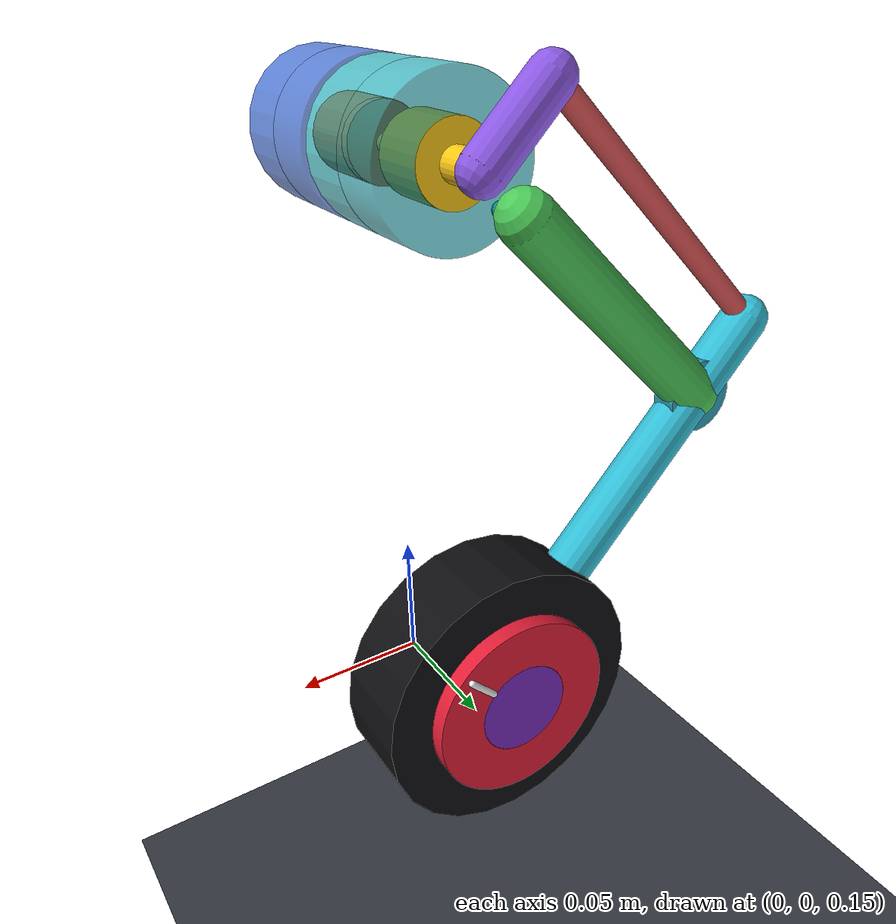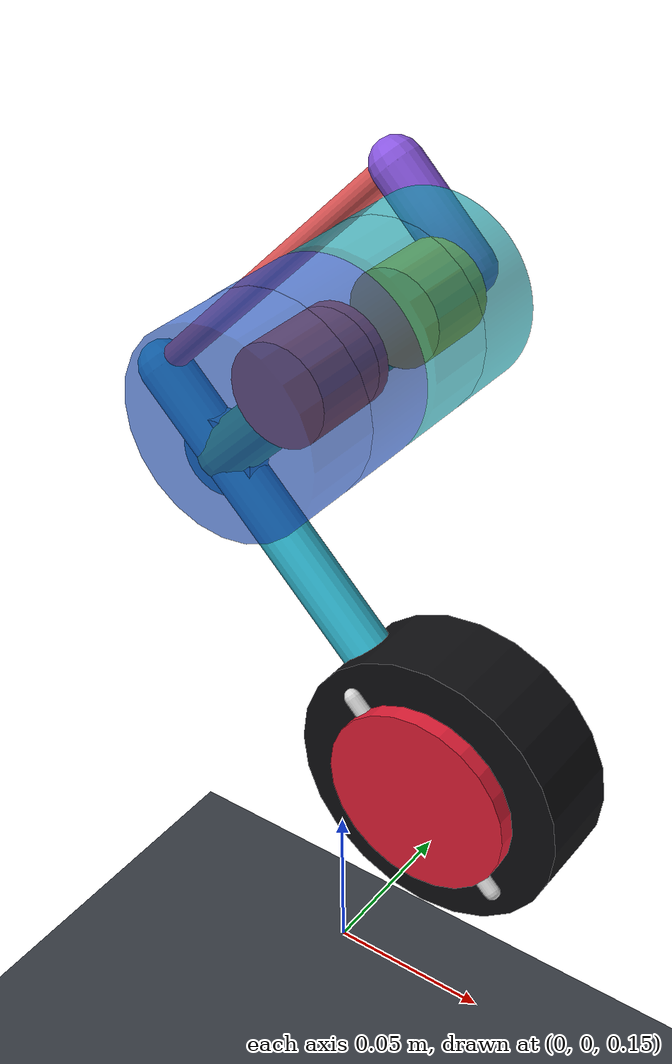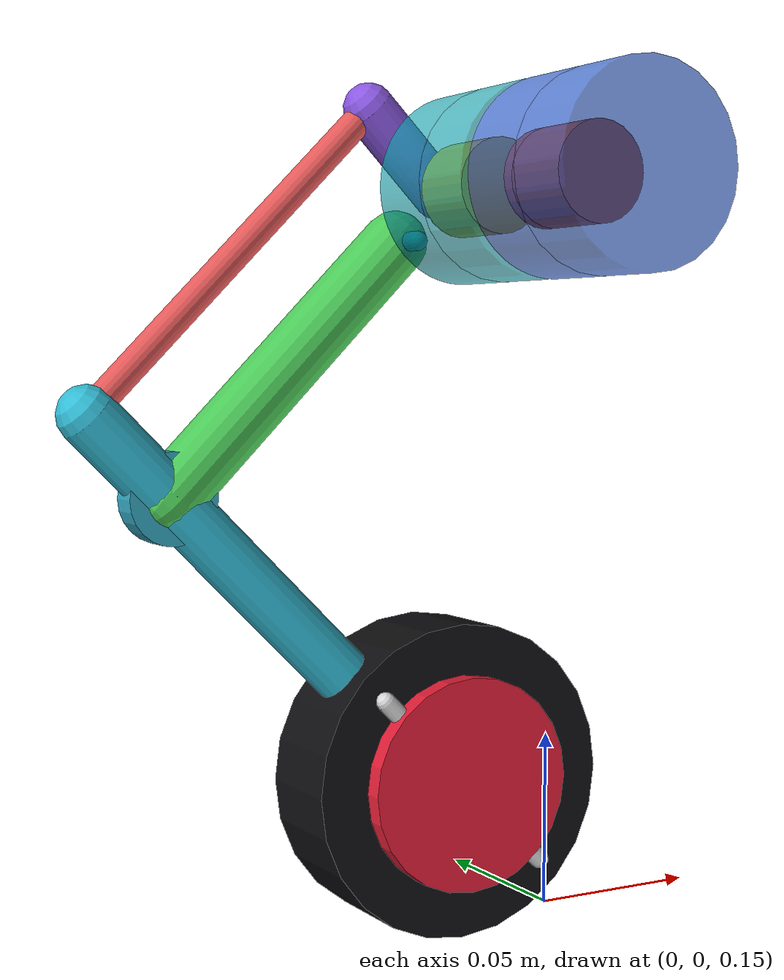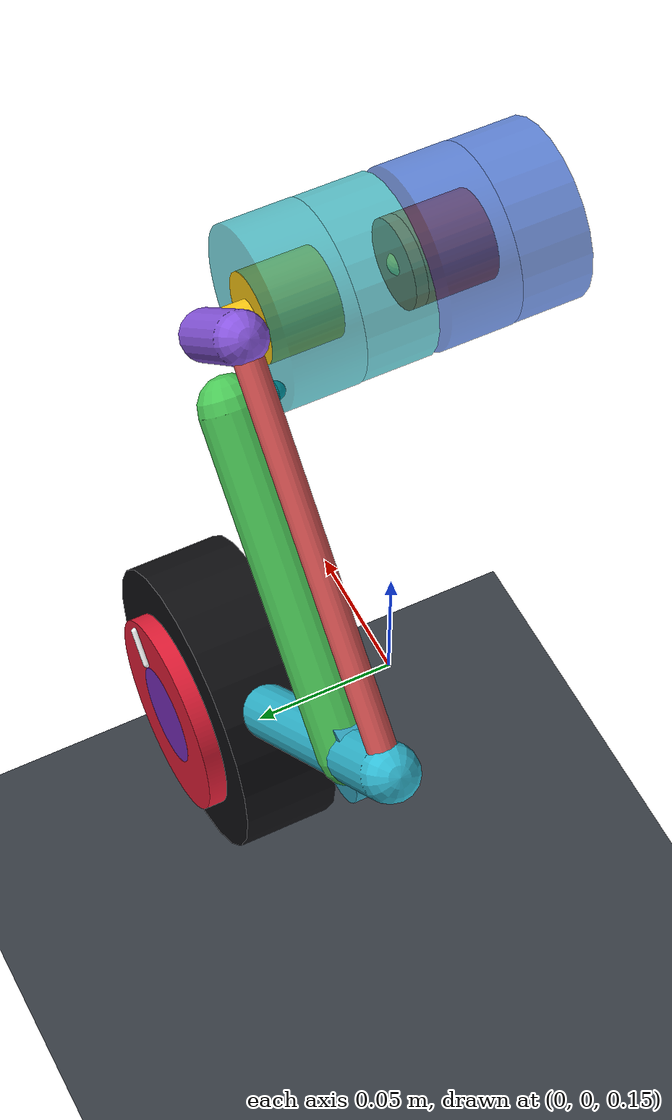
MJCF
<mujoco model="coaxial_parallelogram_wheel_leg_bench">
  <compiler angle="radian" autolimits="true" inertiafromgeom="true" />
  <option timestep="0.001" gravity="0 0 0" integrator="implicitfast" solver="Newton" iterations="100" tolerance="1e-10" />
  <size njmax="200" nconmax="100" />
  <visual>
    <global offwidth="1280" offheight="960" />
    <quality numslices="96" numstacks="32" />
    <headlight ambient="0.45 0.45 0.45" diffuse="0.7 0.7 0.7" />
  </visual>
  <statistic center="-0.04 0 0.295" extent="0.55" />
  <custom>
    <numeric name="geometry" data="0.13 0.035 0.05 0.36" />
    <numeric name="motor_geometry" data="0.057 0.046 0.068 0.0445" />
  </custom>
  <default>
    <joint type="hinge" axis="0 -1 0" damping="0.008" armature="0.00005" />
    <geom contype="0" conaffinity="0" friction="0.8 0.005 0.0001" mass="0" />
    <site size="0.004" rgba="1 0.9 0.2 1" />
    <motor gear="1" ctrllimited="true" />
  </default>
  <worldbody>
    <light pos="0 -1 2" dir="0 0 -1" />
    <geom name="floor" type="plane" size="0.7 0.7 0.01" rgba="0.22 0.24 0.27 1" contype="1" conaffinity="1" mass="0" />
    <site name="target_W" pos="0 0.062 0.176152236891" size="0.007" rgba="1 0.55 0.1 0.8" />
    <body name="hip_mount" pos="0 0 0.36">
      <geom name="hip_motor_stator" type="cylinder" pos="0 -0.025 0" size="0.0285 0.023" euler="1.5707963267948966 0 0" mass="0.15" rgba="0 0 0 0" group="3" />
      <site name="O" />
      <body name="leg_carrier" euler="0 0.785398163397 0">
        <joint name="hip" ref="-0.785398163397" range="-1.75 0.35" armature="0.001" />
        <geom name="hip_motor_rotor" type="cylinder" pos="0 0.002 0" size="0.025 0.008" euler="1.5707963267948966 0 0" mass="0.15" rgba="0 0 0 0" group="3" />
        <geom name="hip_knee_flange" type="cylinder" pos="0 0.0 0" size="0.025 0.004" euler="1.5707963267948966 0 0" mass="0.06" rgba="0 0 0 0" />
        <geom name="hip_knee_register" type="cylinder" pos="0 0.002 0" size="0.01215 0.006" euler="1.5707963267948966 0 0" mass="0" rgba="0 0 0 0" />
        <body name="knee_motor" pos="0 0.025 0">
          <geom name="knee_motor_stator" type="cylinder" pos="0 0 0" size="0.0285 0.023" euler="1.5707963267948966 0 0" mass="0.15" rgba="0 0 0 0" group="3" />
          <body name="linkage_base" pos="0 0.037 0">
            <geom name="fixed_arm_OB" type="capsule" fromto="0 0 0 0 0 -0.13" size="0.010" mass="0.104" rgba="0 0 0 0" group="3" />
            <site name="B" pos="0 0 -0.13" />
            <body name="active_arm_OA" euler="0 1.57079632679 0">
              <joint name="knee_drive" ref="-1.57079632679" range="-2.20 -0.90" armature="0.001" solreflimit="0.001 1" solimplimit="0.99 0.999 0.001 0.5 2" />
              <geom name="knee_motor_rotor" type="cylinder" pos="0 -0.037 0" size="0.025 0.008" euler="1.5707963267948966 0 0" mass="0.15" rgba="0 0 0 0" group="3" />
              <geom name="knee_output_shaft" type="cylinder" pos="0 -0.006999999999999999 0" size=".006 0.006999999999999999" euler="1.5707963267948966 0 0" mass="0" rgba="1 .80 .08 1" />
              <geom name="knee_output_flange" type="cylinder" pos="0 -0.037 0" size="0.025 0.003" euler="1.5707963267948966 0 0" mass="0" rgba="0 0 0 0" group="3" />
              <geom name="active_arm_OA" type="capsule" fromto="0 0 0 0 0 -0.035" size="0.008" mass="0.04" rgba="0.55 0.35 0.90 1" />
              <site name="A" pos="0 0 -0.035" />
              <body name="coupler_AC" pos="0 0 -0.035" euler="0 -1.57079632679 0">
                <joint name="bearing_A" ref="1.57079632679" range="0.60 2.45" />
                <geom name="coupler_AC" type="capsule" fromto="0 0 0 0 0 -0.13" size="0.0045" mass="0.04333333333333334" rgba="0.90 0.35 0.35 1" />
                <site name="C_AC" pos="0 0 -0.13" size="0.0025" rgba="1 1 1 1" />
              </body>
              <geom name="knee_rotor_cap" type="cylinder" pos="0 -0.0255 0" size="0.01425 0.0115" euler="1.5707963267948966 0 0" mass="0" rgba="1 0.80 0.08 1" />
              <geom name="knee_rotor_mark" type="capsule" fromto="0.0078375 -0.013499999999999998 0 0.012825000000000001 -0.013499999999999998 0" size="0.0012" mass="0" rgba="1 1 1 1" />
            </body>
            <body name="output_link_BCW" pos="0 0 -0.13" euler="0 -1.57079632679 0">
              <joint name="bearing_B" ref="1.57079632679" range="0.60 2.45" />
              <geom name="rigid_link_BCW" type="capsule" fromto="0 0 0.035 0 0 -0.13" size="0.009" mass="0.14270270270270272" rgba="0.20 0.75 0.85 1" />
              <geom name="output_bearing_boss" type="cylinder" pos="0 0 0" size="0.014 0.005" euler="1.5707963267948966 0 0" mass="0.012" rgba="0.20 0.65 0.75 1" />
              <geom name="wheel_carrier" type="capsule" fromto="0 -0.012 -0.13 0 0.012 -0.13" size="0.005" mass="0.015" rgba="0.20 0.65 0.75 1" />
              <site name="C_BC" pos="0 0 0.035" size="0.0025" rgba="1 1 1 1" />
              <site name="W" pos="0 0 -0.13" />
              <geom name="hub_motor_stator" type="cylinder" pos="0 0 -0.13" size="0.034 0.02225" euler="1.5707963267948966 0 0" mass="0.18" rgba="0 0 0 0" group="3" />
              <geom name="hub_motor_stator_face" type="cylinder" pos="0 -0.024 -0.13" size="0.0165 0.003" euler="1.5707963267948966 0 0" mass="0" rgba="0 0 0 0" group="3" />
              <body name="wheel" pos="0 0 -0.13">
                <joint name="wheel_spin" axis="0 1 0" limited="false" damping="0.002" armature="0.0001" />
                <geom name="tire" type="cylinder" size="0.05 0.016" euler="1.5707963267948966 0 0" mass="0.26" rgba="0.06 0.06 0.07 1" contype="1" conaffinity="1" condim="3" />
                <geom name="wheel_rim" type="cylinder" size="0.043 0.012" euler="1.5707963267948966 0 0" mass="0.14" rgba="0.34 0.35 0.38 1" />
                <geom name="hub_motor_rotor" type="cylinder" size="0.034 0.02225" euler="1.5707963267948966 0 0" mass="0.18" rgba="0 0 0 0" group="3" />
                <geom name="hub_motor_rotor_face" type="cylinder" pos="0 0.024 0" size="0.0165 0.003" euler="1.5707963267948966 0 0" mass="0" rgba="0 0 0 0" group="3" />
                <geom name="wheel_spoke" type="capsule" fromto="0 -0.017 -0.04000000000000001 0 -0.017 0.04000000000000001" size="0.003" mass="0" rgba="0.85 0.85 0.85 1" />
                <geom name="hub_rotor_cap_back" type="cylinder" pos="0 -0.011125 0" size="0.034 0.011125" euler="1.5707963267948966 0 0" mass="0" rgba="0.90 0.12 0.22 1" />
                <geom name="hub_rotor_cap" type="mesh" mesh="procedural_h6215_ring" pos="0 0 0" mass="0" rgba="0.90 0.12 0.22 1" />
                <geom name="hub_rotor_mark" type="capsule" fromto="0.0187 0.02275 0 0.030600000000000002 0.02275 0" size="0.0012" mass="0" rgba="1 1 1 1" />
              </body>
              <geom name="hub_stator_shell" type="cylinder" pos="0 0.011125 -0.13" size="0.017 0.011125" euler="1.5707963267948966 0 0" mass="0" rgba="0.48 0.18 0.75 1" />
            </body>
            <geom name="fixed_arm_OB_visual" type="capsule" fromto="0 0 -0.022 0 0 -0.13" size=".010" mass="0" rgba=".30 .80 .35 1" />
            <geom name="knee_stator_OB_bracket" type="capsule" fromto="0 -0.013999999999999999 -0.022 0 0 -0.022" size=".003" mass="0" rgba=".04 .65 .70 1" />
          </body>
          <geom name="knee_stator_shell_back" type="cylinder" pos="0 -0.0115 0" size="0.0285 0.0115" euler="1.5707963267948966 0 0" mass="0" rgba="0.04 0.65 0.70 0.65" />
          <geom name="knee_stator_shell" type="mesh" mesh="procedural_j4310_ring" pos="0 0 0" mass="0" rgba="0.04 0.65 0.70 0.65" />
        </body>
        <geom name="hip_rotor_cap" type="cylinder" pos="0 -0.0135 0" size="0.01425 0.0115" euler="1.5707963267948966 0 0" mass="0" rgba="1 0.38 0.06 1" />
        <geom name="hip_rotor_mark" type="capsule" fromto="0.0078375 -0.0015000000000000018 0 0.012825000000000001 -0.0015000000000000018 0" size="0.0012" mass="0" rgba="1 1 1 1" />
        <geom name="hip_rotor_coupling" type="cylinder" pos="0 0 0" size="0.01425 0.002" euler="1.5707963267948966 0 0" mass="0" rgba="1 0.38 0.06 1" />
      </body>
      <geom name="hip_stator_shell_back" type="cylinder" pos="0 -0.0365 0" size="0.0285 0.0115" euler="1.5707963267948966 0 0" mass="0" rgba="0.08 0.30 0.80 0.65" />
      <geom name="hip_stator_shell" type="mesh" mesh="procedural_j4310_ring" pos="0 -0.025 0" mass="0" rgba="0.08 0.30 0.80 0.65" />
    </body>
  </worldbody>
  <equality>
    <connect name="loop_C" site1="C_AC" site2="C_BC" solref="0.004 1" solimp="0.95 0.99 0.001" />
  </equality>
  <actuator>
    <motor name="hip_motor" joint="hip" ctrlrange="-7.0 7.0" />
    <motor name="knee_motor" joint="knee_drive" ctrlrange="-7.0 7.0" />
    <motor name="wheel_motor" joint="wheel_spin" ctrlrange="-2 2" />
  </actuator>
  <asset>
    <mesh name="procedural_j4310_ring" vertex="0.0285 0 0 0.0284656705018 0 0.00139842871833 0.0283627647102 0 0.00279348849939 0.028191530534 0 0.00418181852198 0.0279523804915 0 0.00556007417746 0.027645890716 0 0.00692493512724 0.0272727995684 0 0.00827311330175 0.0268340058577 0 0.00960136082168 0.0263305666766 0 0.0109064778224 0.025763694854 0 0.0121853201628 0.0251347560339 0 0.0134348069995 0.024445265385 0 0.0146519282095 0.0236968839506 0 0.0158337516411 0.0228914146472 0 0.016977430178 0.0220307979208 0 0.0180802085987 0.0211171070726 0 0.0191394302131 0.0201525432638 0 0.0201525432638 0.0191394302131 0 0.0211171070726 0.0180802085987 0 0.0220307979208 0.016977430178 0 0.0228914146472 0.0158337516411 0 0.0236968839506 0.0146519282095 0 0.024445265385 0.0134348069995 0 0.0251347560339 0.0121853201628 0 0.025763694854 0.0109064778224 0 0.0263305666766 0.00960136082168 0 0.0268340058577 0.00827311330175 0 0.0272727995684 0.00692493512724 0 0.027645890716 0.00556007417746 0 0.0279523804915 0.00418181852198 0 0.028191530534 0.00279348849939 0 0.0283627647102 0.00139842871833 0 0.0284656705018 1.74512168878e-18 0 0.0285 -0.00139842871833 0 0.0284656705018 -0.00279348849939 0 0.0283627647102 -0.00418181852198 0 0.028191530534 -0.00556007417746 0 0.0279523804915 -0.00692493512724 0 0.027645890716 -0.00827311330175 0 0.0272727995684 -0.00960136082168 0 0.0268340058577 -0.0109064778224 0 0.0263305666766 -0.0121853201628 0 0.025763694854 -0.0134348069995 0 0.0251347560339 -0.0146519282095 0 0.024445265385 -0.0158337516411 0 0.0236968839506 -0.016977430178 0 0.0228914146472 -0.0180802085987 0 0.0220307979208 -0.0191394302131 0 0.0211171070726 -0.0201525432638 0 0.0201525432638 -0.0211171070726 0 0.0191394302131 -0.0220307979208 0 0.0180802085987 -0.0228914146472 0 0.016977430178 -0.0236968839506 0 0.0158337516411 -0.024445265385 0 0.0146519282095 -0.0251347560339 0 0.0134348069995 -0.025763694854 0 0.0121853201628 -0.0263305666766 0 0.0109064778224 -0.0268340058577 0 0.00960136082168 -0.0272727995684 0 0.00827311330175 -0.027645890716 0 0.00692493512724 -0.0279523804915 0 0.00556007417746 -0.028191530534 0 0.00418181852198 -0.0283627647102 0 0.00279348849939 -0.0284656705018 0 0.00139842871833 -0.0285 0 3.49024337757e-18 -0.0284656705018 0 -0.00139842871833 -0.0283627647102 0 -0.00279348849939 -0.028191530534 0 -0.00418181852198 -0.0279523804915 0 -0.00556007417746 -0.027645890716 0 -0.00692493512724 -0.0272727995684 0 -0.00827311330175 -0.0268340058577 0 -0.00960136082168 -0.0263305666766 0 -0.0109064778224 -0.025763694854 0 -0.0121853201628 -0.0251347560339 0 -0.0134348069995 -0.024445265385 0 -0.0146519282095 -0.0236968839506 0 -0.0158337516411 -0.0228914146472 0 -0.016977430178 -0.0220307979208 0 -0.0180802085987 -0.0211171070726 0 -0.0191394302131 -0.0201525432638 0 -0.0201525432638 -0.0191394302131 0 -0.0211171070726 -0.0180802085987 0 -0.0220307979208 -0.016977430178 0 -0.0228914146472 -0.0158337516411 0 -0.0236968839506 -0.0146519282095 0 -0.024445265385 -0.0134348069995 0 -0.0251347560339 -0.0121853201628 0 -0.025763694854 -0.0109064778224 0 -0.0263305666766 -0.00960136082168 0 -0.0268340058577 -0.00827311330175 0 -0.0272727995684 -0.00692493512724 0 -0.027645890716 -0.00556007417746 0 -0.0279523804915 -0.00418181852198 0 -0.028191530534 -0.00279348849939 0 -0.0283627647102 -0.00139842871833 0 -0.0284656705018 -5.23536506635e-18 0 -0.0285 0.00139842871833 0 -0.0284656705018 0.00279348849939 0 -0.0283627647102 0.00418181852198 0 -0.028191530534 0.00556007417746 0 -0.0279523804915 0.00692493512724 0 -0.027645890716 0.00827311330175 0 -0.0272727995684 0.00960136082168 0 -0.0268340058577 0.0109064778224 0 -0.0263305666766 0.0121853201628 0 -0.025763694854 0.0134348069995 0 -0.0251347560339 0.0146519282095 0 -0.024445265385 0.0158337516411 0 -0.0236968839506 0.016977430178 0 -0.0228914146472 0.0180802085987 0 -0.0220307979208 0.0191394302131 0 -0.0211171070726 0.0201525432638 0 -0.0201525432638 0.0211171070726 0 -0.0191394302131 0.0220307979208 0 -0.0180802085987 0.0228914146472 0 -0.016977430178 0.0236968839506 0 -0.0158337516411 0.024445265385 0 -0.0146519282095 0.0251347560339 0 -0.0134348069995 0.025763694854 0 -0.0121853201628 0.0263305666766 0 -0.0109064778224 0.0268340058577 0 -0.00960136082168 0.0272727995684 0 -0.00827311330175 0.027645890716 0 -0.00692493512724 0.0279523804915 0 -0.00556007417746 0.028191530534 0 -0.00418181852198 0.0283627647102 0 -0.00279348849939 0.0284656705018 0 -0.00139842871833 0.0285 0.023 0 0.0284656705018 0.023 0.00139842871833 0.0283627647102 0.023 0.00279348849939 0.028191530534 0.023 0.00418181852198 0.0279523804915 0.023 0.00556007417746 0.027645890716 0.023 0.00692493512724 0.0272727995684 0.023 0.00827311330175 0.0268340058577 0.023 0.00960136082168 0.0263305666766 0.023 0.0109064778224 0.025763694854 0.023 0.0121853201628 0.0251347560339 0.023 0.0134348069995 0.024445265385 0.023 0.0146519282095 0.0236968839506 0.023 0.0158337516411 0.0228914146472 0.023 0.016977430178 0.0220307979208 0.023 0.0180802085987 0.0211171070726 0.023 0.0191394302131 0.0201525432638 0.023 0.0201525432638 0.0191394302131 0.023 0.0211171070726 0.0180802085987 0.023 0.0220307979208 0.016977430178 0.023 0.0228914146472 0.0158337516411 0.023 0.0236968839506 0.0146519282095 0.023 0.024445265385 0.0134348069995 0.023 0.0251347560339 0.0121853201628 0.023 0.025763694854 0.0109064778224 0.023 0.0263305666766 0.00960136082168 0.023 0.0268340058577 0.00827311330175 0.023 0.0272727995684 0.00692493512724 0.023 0.027645890716 0.00556007417746 0.023 0.0279523804915 0.00418181852198 0.023 0.028191530534 0.00279348849939 0.023 0.0283627647102 0.00139842871833 0.023 0.0284656705018 1.74512168878e-18 0.023 0.0285 -0.00139842871833 0.023 0.0284656705018 -0.00279348849939 0.023 0.0283627647102 -0.00418181852198 0.023 0.028191530534 -0.00556007417746 0.023 0.0279523804915 -0.00692493512724 0.023 0.027645890716 -0.00827311330175 0.023 0.0272727995684 -0.00960136082168 0.023 0.0268340058577 -0.0109064778224 0.023 0.0263305666766 -0.0121853201628 0.023 0.025763694854 -0.0134348069995 0.023 0.0251347560339 -0.0146519282095 0.023 0.024445265385 -0.0158337516411 0.023 0.0236968839506 -0.016977430178 0.023 0.0228914146472 -0.0180802085987 0.023 0.0220307979208 -0.0191394302131 0.023 0.0211171070726 -0.0201525432638 0.023 0.0201525432638 -0.0211171070726 0.023 0.0191394302131 -0.0220307979208 0.023 0.0180802085987 -0.0228914146472 0.023 0.016977430178 -0.0236968839506 0.023 0.0158337516411 -0.024445265385 0.023 0.0146519282095 -0.0251347560339 0.023 0.0134348069995 -0.025763694854 0.023 0.0121853201628 -0.0263305666766 0.023 0.0109064778224 -0.0268340058577 0.023 0.00960136082168 -0.0272727995684 0.023 0.00827311330175 -0.027645890716 0.023 0.00692493512724 -0.0279523804915 0.023 0.00556007417746 -0.028191530534 0.023 0.00418181852198 -0.0283627647102 0.023 0.00279348849939 -0.0284656705018 0.023 0.00139842871833 -0.0285 0.023 3.49024337757e-18 -0.0284656705018 0.023 -0.00139842871833 -0.0283627647102 0.023 -0.00279348849939 -0.028191530534 0.023 -0.00418181852198 -0.0279523804915 0.023 -0.00556007417746 -0.027645890716 0.023 -0.00692493512724 -0.0272727995684 0.023 -0.00827311330175 -0.0268340058577 0.023 -0.00960136082168 -0.0263305666766 0.023 -0.0109064778224 -0.025763694854 0.023 -0.0121853201628 -0.0251347560339 0.023 -0.0134348069995 -0.024445265385 0.023 -0.0146519282095 -0.0236968839506 0.023 -0.0158337516411 -0.0228914146472 0.023 -0.016977430178 -0.0220307979208 0.023 -0.0180802085987 -0.0211171070726 0.023 -0.0191394302131 -0.0201525432638 0.023 -0.0201525432638 -0.0191394302131 0.023 -0.0211171070726 -0.0180802085987 0.023 -0.0220307979208 -0.016977430178 0.023 -0.0228914146472 -0.0158337516411 0.023 -0.0236968839506 -0.0146519282095 0.023 -0.024445265385 -0.0134348069995 0.023 -0.0251347560339 -0.0121853201628 0.023 -0.025763694854 -0.0109064778224 0.023 -0.0263305666766 -0.00960136082168 0.023 -0.0268340058577 -0.00827311330175 0.023 -0.0272727995684 -0.00692493512724 0.023 -0.027645890716 -0.00556007417746 0.023 -0.0279523804915 -0.00418181852198 0.023 -0.028191530534 -0.00279348849939 0.023 -0.0283627647102 -0.00139842871833 0.023 -0.0284656705018 -5.23536506635e-18 0.023 -0.0285 0.00139842871833 0.023 -0.0284656705018 0.00279348849939 0.023 -0.0283627647102 0.00418181852198 0.023 -0.028191530534 0.00556007417746 0.023 -0.0279523804915 0.00692493512724 0.023 -0.027645890716 0.00827311330175 0.023 -0.0272727995684 0.00960136082168 0.023 -0.0268340058577 0.0109064778224 0.023 -0.0263305666766 0.0121853201628 0.023 -0.025763694854 0.0134348069995 0.023 -0.0251347560339 0.0146519282095 0.023 -0.024445265385 0.0158337516411 0.023 -0.0236968839506 0.016977430178 0.023 -0.0228914146472 0.0180802085987 0.023 -0.0220307979208 0.0191394302131 0.023 -0.0211171070726 0.0201525432638 0.023 -0.0201525432638 0.0211171070726 0.023 -0.0191394302131 0.0220307979208 0.023 -0.0180802085987 0.0228914146472 0.023 -0.016977430178 0.0236968839506 0.023 -0.0158337516411 0.024445265385 0.023 -0.0146519282095 0.0251347560339 0.023 -0.0134348069995 0.025763694854 0.023 -0.0121853201628 0.0263305666766 0.023 -0.0109064778224 0.0268340058577 0.023 -0.00960136082168 0.0272727995684 0.023 -0.00827311330175 0.027645890716 0.023 -0.00692493512724 0.0279523804915 0.023 -0.00556007417746 0.028191530534 0.023 -0.00418181852198 0.0283627647102 0.023 -0.00279348849939 0.0284656705018 0.023 -0.00139842871833 0.01425 0 0 0.0142328352509 0 0.000699214359166 0.0141813823551 0 0.0013967442497 0.014095765267 0 0.00209090926099 0.0139761902457 0 0.00278003708873 0.013822945358 0 0.00346246756362 0.0136363997842 0 0.00413655665088 0.0134170029289 0 0.00480068041084 0.0131652833383 0 0.0054532389112 0.012881847427 0 0.00609266008138 0.012567378017 0 0.00671740349977 0.0122226326925 0 0.00732596410475 0.0118484419753 0 0.00791687582053 0.0114457073236 0 0.00848871508902 0.0110153989604 0 0.00904010429933 0.0105585535363 0 0.00956971510657 0.0100762716319 0 0.0100762716319 0.00956971510657 0 0.0105585535363 0.00904010429933 0 0.0110153989604 0.00848871508902 0 0.0114457073236 0.00791687582053 0 0.0118484419753 0.00732596410475 0 0.0122226326925 0.00671740349977 0 0.012567378017 0.00609266008138 0 0.012881847427 0.0054532389112 0 0.0131652833383 0.00480068041084 0 0.0134170029289 0.00413655665088 0 0.0136363997842 0.00346246756362 0 0.013822945358 0.00278003708873 0 0.0139761902457 0.00209090926099 0 0.014095765267 0.0013967442497 0 0.0141813823551 0.000699214359166 0 0.0142328352509 8.72560844392e-19 0 0.01425 -0.000699214359166 0 0.0142328352509 -0.0013967442497 0 0.0141813823551 -0.00209090926099 0 0.014095765267 -0.00278003708873 0 0.0139761902457 -0.00346246756362 0 0.013822945358 -0.00413655665088 0 0.0136363997842 -0.00480068041084 0 0.0134170029289 -0.0054532389112 0 0.0131652833383 -0.00609266008138 0 0.012881847427 -0.00671740349977 0 0.012567378017 -0.00732596410475 0 0.0122226326925 -0.00791687582053 0 0.0118484419753 -0.00848871508902 0 0.0114457073236 -0.00904010429933 0 0.0110153989604 -0.00956971510657 0 0.0105585535363 -0.0100762716319 0 0.0100762716319 -0.0105585535363 0 0.00956971510657 -0.0110153989604 0 0.00904010429933 -0.0114457073236 0 0.00848871508902 -0.0118484419753 0 0.00791687582053 -0.0122226326925 0 0.00732596410475 -0.012567378017 0 0.00671740349977 -0.012881847427 0 0.00609266008138 -0.0131652833383 0 0.0054532389112 -0.0134170029289 0 0.00480068041084 -0.0136363997842 0 0.00413655665088 -0.013822945358 0 0.00346246756362 -0.0139761902457 0 0.00278003708873 -0.014095765267 0 0.00209090926099 -0.0141813823551 0 0.0013967442497 -0.0142328352509 0 0.000699214359166 -0.01425 0 1.74512168878e-18 -0.0142328352509 0 -0.000699214359166 -0.0141813823551 0 -0.0013967442497 -0.014095765267 0 -0.00209090926099 -0.0139761902457 0 -0.00278003708873 -0.013822945358 0 -0.00346246756362 -0.0136363997842 0 -0.00413655665088 -0.0134170029289 0 -0.00480068041084 -0.0131652833383 0 -0.0054532389112 -0.012881847427 0 -0.00609266008138 -0.012567378017 0 -0.00671740349977 -0.0122226326925 0 -0.00732596410475 -0.0118484419753 0 -0.00791687582053 -0.0114457073236 0 -0.00848871508902 -0.0110153989604 0 -0.00904010429933 -0.0105585535363 0 -0.00956971510657 -0.0100762716319 0 -0.0100762716319 -0.00956971510657 0 -0.0105585535363 -0.00904010429933 0 -0.0110153989604 -0.00848871508902 0 -0.0114457073236 -0.00791687582053 0 -0.0118484419753 -0.00732596410475 0 -0.0122226326925 -0.00671740349977 0 -0.012567378017 -0.00609266008138 0 -0.012881847427 -0.0054532389112 0 -0.0131652833383 -0.00480068041084 0 -0.0134170029289 -0.00413655665088 0 -0.0136363997842 -0.00346246756362 0 -0.013822945358 -0.00278003708873 0 -0.0139761902457 -0.00209090926099 0 -0.014095765267 -0.0013967442497 0 -0.0141813823551 -0.000699214359166 0 -0.0142328352509 -2.61768253318e-18 0 -0.01425 0.000699214359166 0 -0.0142328352509 0.0013967442497 0 -0.0141813823551 0.00209090926099 0 -0.014095765267 0.00278003708873 0 -0.0139761902457 0.00346246756362 0 -0.013822945358 0.00413655665088 0 -0.0136363997842 0.00480068041084 0 -0.0134170029289 0.0054532389112 0 -0.0131652833383 0.00609266008138 0 -0.012881847427 0.00671740349977 0 -0.012567378017 0.00732596410475 0 -0.0122226326925 0.00791687582053 0 -0.0118484419753 0.00848871508902 0 -0.0114457073236 0.00904010429933 0 -0.0110153989604 0.00956971510657 0 -0.0105585535363 0.0100762716319 0 -0.0100762716319 0.0105585535363 0 -0.00956971510657 0.0110153989604 0 -0.00904010429933 0.0114457073236 0 -0.00848871508902 0.0118484419753 0 -0.00791687582053 0.0122226326925 0 -0.00732596410475 0.012567378017 0 -0.00671740349977 0.012881847427 0 -0.00609266008138 0.0131652833383 0 -0.0054532389112 0.0134170029289 0 -0.00480068041084 0.0136363997842 0 -0.00413655665088 0.013822945358 0 -0.00346246756362 0.0139761902457 0 -0.00278003708873 0.014095765267 0 -0.00209090926099 0.0141813823551 0 -0.0013967442497 0.0142328352509 0 -0.000699214359166 0.01425 0.023 0 0.0142328352509 0.023 0.000699214359166 0.0141813823551 0.023 0.0013967442497 0.014095765267 0.023 0.00209090926099 0.0139761902457 0.023 0.00278003708873 0.013822945358 0.023 0.00346246756362 0.0136363997842 0.023 0.00413655665088 0.0134170029289 0.023 0.00480068041084 0.0131652833383 0.023 0.0054532389112 0.012881847427 0.023 0.00609266008138 0.012567378017 0.023 0.00671740349977 0.0122226326925 0.023 0.00732596410475 0.0118484419753 0.023 0.00791687582053 0.0114457073236 0.023 0.00848871508902 0.0110153989604 0.023 0.00904010429933 0.0105585535363 0.023 0.00956971510657 0.0100762716319 0.023 0.0100762716319 0.00956971510657 0.023 0.0105585535363 0.00904010429933 0.023 0.0110153989604 0.00848871508902 0.023 0.0114457073236 0.00791687582053 0.023 0.0118484419753 0.00732596410475 0.023 0.0122226326925 0.00671740349977 0.023 0.012567378017 0.00609266008138 0.023 0.012881847427 0.0054532389112 0.023 0.0131652833383 0.00480068041084 0.023 0.0134170029289 0.00413655665088 0.023 0.0136363997842 0.00346246756362 0.023 0.013822945358 0.00278003708873 0.023 0.0139761902457 0.00209090926099 0.023 0.014095765267 0.0013967442497 0.023 0.0141813823551 0.000699214359166 0.023 0.0142328352509 8.72560844392e-19 0.023 0.01425 -0.000699214359166 0.023 0.0142328352509 -0.0013967442497 0.023 0.0141813823551 -0.00209090926099 0.023 0.014095765267 -0.00278003708873 0.023 0.0139761902457 -0.00346246756362 0.023 0.013822945358 -0.00413655665088 0.023 0.0136363997842 -0.00480068041084 0.023 0.0134170029289 -0.0054532389112 0.023 0.0131652833383 -0.00609266008138 0.023 0.012881847427 -0.00671740349977 0.023 0.012567378017 -0.00732596410475 0.023 0.0122226326925 -0.00791687582053 0.023 0.0118484419753 -0.00848871508902 0.023 0.0114457073236 -0.00904010429933 0.023 0.0110153989604 -0.00956971510657 0.023 0.0105585535363 -0.0100762716319 0.023 0.0100762716319 -0.0105585535363 0.023 0.00956971510657 -0.0110153989604 0.023 0.00904010429933 -0.0114457073236 0.023 0.00848871508902 -0.0118484419753 0.023 0.00791687582053 -0.0122226326925 0.023 0.00732596410475 -0.012567378017 0.023 0.00671740349977 -0.012881847427 0.023 0.00609266008138 -0.0131652833383 0.023 0.0054532389112 -0.0134170029289 0.023 0.00480068041084 -0.0136363997842 0.023 0.00413655665088 -0.013822945358 0.023 0.00346246756362 -0.0139761902457 0.023 0.00278003708873 -0.014095765267 0.023 0.00209090926099 -0.0141813823551 0.023 0.0013967442497 -0.0142328352509 0.023 0.000699214359166 -0.01425 0.023 1.74512168878e-18 -0.0142328352509 0.023 -0.000699214359166 -0.0141813823551 0.023 -0.0013967442497 -0.014095765267 0.023 -0.00209090926099 -0.0139761902457 0.023 -0.00278003708873 -0.013822945358 0.023 -0.00346246756362 -0.0136363997842 0.023 -0.00413655665088 -0.0134170029289 0.023 -0.00480068041084 -0.0131652833383 0.023 -0.0054532389112 -0.012881847427 0.023 -0.00609266008138 -0.012567378017 0.023 -0.00671740349977 -0.0122226326925 0.023 -0.00732596410475 -0.0118484419753 0.023 -0.00791687582053 -0.0114457073236 0.023 -0.00848871508902 -0.0110153989604 0.023 -0.00904010429933 -0.0105585535363 0.023 -0.00956971510657 -0.0100762716319 0.023 -0.0100762716319 -0.00956971510657 0.023 -0.0105585535363 -0.00904010429933 0.023 -0.0110153989604 -0.00848871508902 0.023 -0.0114457073236 -0.00791687582053 0.023 -0.0118484419753 -0.00732596410475 0.023 -0.0122226326925 -0.00671740349977 0.023 -0.012567378017 -0.00609266008138 0.023 -0.012881847427 -0.0054532389112 0.023 -0.0131652833383 -0.00480068041084 0.023 -0.0134170029289 -0.00413655665088 0.023 -0.0136363997842 -0.00346246756362 0.023 -0.013822945358 -0.00278003708873 0.023 -0.0139761902457 -0.00209090926099 0.023 -0.014095765267 -0.0013967442497 0.023 -0.0141813823551 -0.000699214359166 0.023 -0.0142328352509 -2.61768253318e-18 0.023 -0.01425 0.000699214359166 0.023 -0.0142328352509 0.0013967442497 0.023 -0.0141813823551 0.00209090926099 0.023 -0.014095765267 0.00278003708873 0.023 -0.0139761902457 0.00346246756362 0.023 -0.013822945358 0.00413655665088 0.023 -0.0136363997842 0.00480068041084 0.023 -0.0134170029289 0.0054532389112 0.023 -0.0131652833383 0.00609266008138 0.023 -0.012881847427 0.00671740349977 0.023 -0.012567378017 0.00732596410475 0.023 -0.0122226326925 0.00791687582053 0.023 -0.0118484419753 0.00848871508902 0.023 -0.0114457073236 0.00904010429933 0.023 -0.0110153989604 0.00956971510657 0.023 -0.0105585535363 0.0100762716319 0.023 -0.0100762716319 0.0105585535363 0.023 -0.00956971510657 0.0110153989604 0.023 -0.00904010429933 0.0114457073236 0.023 -0.00848871508902 0.0118484419753 0.023 -0.00791687582053 0.0122226326925 0.023 -0.00732596410475 0.012567378017 0.023 -0.00671740349977 0.012881847427 0.023 -0.00609266008138 0.0131652833383 0.023 -0.0054532389112 0.0134170029289 0.023 -0.00480068041084 0.0136363997842 0.023 -0.00413655665088 0.013822945358 0.023 -0.00346246756362 0.0139761902457 0.023 -0.00278003708873 0.014095765267 0.023 -0.00209090926099 0.0141813823551 0.023 -0.0013967442497 0.0142328352509 0.023 -0.000699214359166" face="0 128 129 0 129 1 256 257 385 256 385 384 128 384 385 128 385 129 0 1 257 0 257 256 1 129 130 1 130 2 257 258 386 257 386 385 129 385 386 129 386 130 1 2 258 1 258 257 2 130 131 2 131 3 258 259 387 258 387 386 130 386 387 130 387 131 2 3 259 2 259 258 3 131 132 3 132 4 259 260 388 259 388 387 131 387 388 131 388 132 3 4 260 3 260 259 4 132 133 4 133 5 260 261 389 260 389 388 132 388 389 132 389 133 4 5 261 4 261 260 5 133 134 5 134 6 261 262 390 261 390 389 133 389 390 133 390 134 5 6 262 5 262 261 6 134 135 6 135 7 262 263 391 262 391 390 134 390 391 134 391 135 6 7 263 6 263 262 7 135 136 7 136 8 263 264 392 263 392 391 135 391 392 135 392 136 7 8 264 7 264 263 8 136 137 8 137 9 264 265 393 264 393 392 136 392 393 136 393 137 8 9 265 8 265 264 9 137 138 9 138 10 265 266 394 265 394 393 137 393 394 137 394 138 9 10 266 9 266 265 10 138 139 10 139 11 266 267 395 266 395 394 138 394 395 138 395 139 10 11 267 10 267 266 11 139 140 11 140 12 267 268 396 267 396 395 139 395 396 139 396 140 11 12 268 11 268 267 12 140 141 12 141 13 268 269 397 268 397 396 140 396 397 140 397 141 12 13 269 12 269 268 13 141 142 13 142 14 269 270 398 269 398 397 141 397 398 141 398 142 13 14 270 13 270 269 14 142 143 14 143 15 270 271 399 270 399 398 142 398 399 142 399 143 14 15 271 14 271 270 15 143 144 15 144 16 271 272 400 271 400 399 143 399 400 143 400 144 15 16 272 15 272 271 16 144 145 16 145 17 272 273 401 272 401 400 144 400 401 144 401 145 16 17 273 16 273 272 17 145 146 17 146 18 273 274 402 273 402 401 145 401 402 145 402 146 17 18 274 17 274 273 18 146 147 18 147 19 274 275 403 274 403 402 146 402 403 146 403 147 18 19 275 18 275 274 19 147 148 19 148 20 275 276 404 275 404 403 147 403 404 147 404 148 19 20 276 19 276 275 20 148 149 20 149 21 276 277 405 276 405 404 148 404 405 148 405 149 20 21 277 20 277 276 21 149 150 21 150 22 277 278 406 277 406 405 149 405 406 149 406 150 21 22 278 21 278 277 22 150 151 22 151 23 278 279 407 278 407 406 150 406 407 150 407 151 22 23 279 22 279 278 23 151 152 23 152 24 279 280 408 279 408 407 151 407 408 151 408 152 23 24 280 23 280 279 24 152 153 24 153 25 280 281 409 280 409 408 152 408 409 152 409 153 24 25 281 24 281 280 25 153 154 25 154 26 281 282 410 281 410 409 153 409 410 153 410 154 25 26 282 25 282 281 26 154 155 26 155 27 282 283 411 282 411 410 154 410 411 154 411 155 26 27 283 26 283 282 27 155 156 27 156 28 283 284 412 283 412 411 155 411 412 155 412 156 27 28 284 27 284 283 28 156 157 28 157 29 284 285 413 284 413 412 156 412 413 156 413 157 28 29 285 28 285 284 29 157 158 29 158 30 285 286 414 285 414 413 157 413 414 157 414 158 29 30 286 29 286 285 30 158 159 30 159 31 286 287 415 286 415 414 158 414 415 158 415 159 30 31 287 30 287 286 31 159 160 31 160 32 287 288 416 287 416 415 159 415 416 159 416 160 31 32 288 31 288 287 32 160 161 32 161 33 288 289 417 288 417 416 160 416 417 160 417 161 32 33 289 32 289 288 33 161 162 33 162 34 289 290 418 289 418 417 161 417 418 161 418 162 33 34 290 33 290 289 34 162 163 34 163 35 290 291 419 290 419 418 162 418 419 162 419 163 34 35 291 34 291 290 35 163 164 35 164 36 291 292 420 291 420 419 163 419 420 163 420 164 35 36 292 35 292 291 36 164 165 36 165 37 292 293 421 292 421 420 164 420 421 164 421 165 36 37 293 36 293 292 37 165 166 37 166 38 293 294 422 293 422 421 165 421 422 165 422 166 37 38 294 37 294 293 38 166 167 38 167 39 294 295 423 294 423 422 166 422 423 166 423 167 38 39 295 38 295 294 39 167 168 39 168 40 295 296 424 295 424 423 167 423 424 167 424 168 39 40 296 39 296 295 40 168 169 40 169 41 296 297 425 296 425 424 168 424 425 168 425 169 40 41 297 40 297 296 41 169 170 41 170 42 297 298 426 297 426 425 169 425 426 169 426 170 41 42 298 41 298 297 42 170 171 42 171 43 298 299 427 298 427 426 170 426 427 170 427 171 42 43 299 42 299 298 43 171 172 43 172 44 299 300 428 299 428 427 171 427 428 171 428 172 43 44 300 43 300 299 44 172 173 44 173 45 300 301 429 300 429 428 172 428 429 172 429 173 44 45 301 44 301 300 45 173 174 45 174 46 301 302 430 301 430 429 173 429 430 173 430 174 45 46 302 45 302 301 46 174 175 46 175 47 302 303 431 302 431 430 174 430 431 174 431 175 46 47 303 46 303 302 47 175 176 47 176 48 303 304 432 303 432 431 175 431 432 175 432 176 47 48 304 47 304 303 48 176 177 48 177 49 304 305 433 304 433 432 176 432 433 176 433 177 48 49 305 48 305 304 49 177 178 49 178 50 305 306 434 305 434 433 177 433 434 177 434 178 49 50 306 49 306 305 50 178 179 50 179 51 306 307 435 306 435 434 178 434 435 178 435 179 50 51 307 50 307 306 51 179 180 51 180 52 307 308 436 307 436 435 179 435 436 179 436 180 51 52 308 51 308 307 52 180 181 52 181 53 308 309 437 308 437 436 180 436 437 180 437 181 52 53 309 52 309 308 53 181 182 53 182 54 309 310 438 309 438 437 181 437 438 181 438 182 53 54 310 53 310 309 54 182 183 54 183 55 310 311 439 310 439 438 182 438 439 182 439 183 54 55 311 54 311 310 55 183 184 55 184 56 311 312 440 311 440 439 183 439 440 183 440 184 55 56 312 55 312 311 56 184 185 56 185 57 312 313 441 312 441 440 184 440 441 184 441 185 56 57 313 56 313 312 57 185 186 57 186 58 313 314 442 313 442 441 185 441 442 185 442 186 57 58 314 57 314 313 58 186 187 58 187 59 314 315 443 314 443 442 186 442 443 186 443 187 58 59 315 58 315 314 59 187 188 59 188 60 315 316 444 315 444 443 187 443 444 187 444 188 59 60 316 59 316 315 60 188 189 60 189 61 316 317 445 316 445 444 188 444 445 188 445 189 60 61 317 60 317 316 61 189 190 61 190 62 317 318 446 317 446 445 189 445 446 189 446 190 61 62 318 61 318 317 62 190 191 62 191 63 318 319 447 318 447 446 190 446 447 190 447 191 62 63 319 62 319 318 63 191 192 63 192 64 319 320 448 319 448 447 191 447 448 191 448 192 63 64 320 63 320 319 64 192 193 64 193 65 320 321 449 320 449 448 192 448 449 192 449 193 64 65 321 64 321 320 65 193 194 65 194 66 321 322 450 321 450 449 193 449 450 193 450 194 65 66 322 65 322 321 66 194 195 66 195 67 322 323 451 322 451 450 194 450 451 194 451 195 66 67 323 66 323 322 67 195 196 67 196 68 323 324 452 323 452 451 195 451 452 195 452 196 67 68 324 67 324 323 68 196 197 68 197 69 324 325 453 324 453 452 196 452 453 196 453 197 68 69 325 68 325 324 69 197 198 69 198 70 325 326 454 325 454 453 197 453 454 197 454 198 69 70 326 69 326 325 70 198 199 70 199 71 326 327 455 326 455 454 198 454 455 198 455 199 70 71 327 70 327 326 71 199 200 71 200 72 327 328 456 327 456 455 199 455 456 199 456 200 71 72 328 71 328 327 72 200 201 72 201 73 328 329 457 328 457 456 200 456 457 200 457 201 72 73 329 72 329 328 73 201 202 73 202 74 329 330 458 329 458 457 201 457 458 201 458 202 73 74 330 73 330 329 74 202 203 74 203 75 330 331 459 330 459 458 202 458 459 202 459 203 74 75 331 74 331 330 75 203 204 75 204 76 331 332 460 331 460 459 203 459 460 203 460 204 75 76 332 75 332 331 76 204 205 76 205 77 332 333 461 332 461 460 204 460 461 204 461 205 76 77 333 76 333 332 77 205 206 77 206 78 333 334 462 333 462 461 205 461 462 205 462 206 77 78 334 77 334 333 78 206 207 78 207 79 334 335 463 334 463 462 206 462 463 206 463 207 78 79 335 78 335 334 79 207 208 79 208 80 335 336 464 335 464 463 207 463 464 207 464 208 79 80 336 79 336 335 80 208 209 80 209 81 336 337 465 336 465 464 208 464 465 208 465 209 80 81 337 80 337 336 81 209 210 81 210 82 337 338 466 337 466 465 209 465 466 209 466 210 81 82 338 81 338 337 82 210 211 82 211 83 338 339 467 338 467 466 210 466 467 210 467 211 82 83 339 82 339 338 83 211 212 83 212 84 339 340 468 339 468 467 211 467 468 211 468 212 83 84 340 83 340 339 84 212 213 84 213 85 340 341 469 340 469 468 212 468 469 212 469 213 84 85 341 84 341 340 85 213 214 85 214 86 341 342 470 341 470 469 213 469 470 213 470 214 85 86 342 85 342 341 86 214 215 86 215 87 342 343 471 342 471 470 214 470 471 214 471 215 86 87 343 86 343 342 87 215 216 87 216 88 343 344 472 343 472 471 215 471 472 215 472 216 87 88 344 87 344 343 88 216 217 88 217 89 344 345 473 344 473 472 216 472 473 216 473 217 88 89 345 88 345 344 89 217 218 89 218 90 345 346 474 345 474 473 217 473 474 217 474 218 89 90 346 89 346 345 90 218 219 90 219 91 346 347 475 346 475 474 218 474 475 218 475 219 90 91 347 90 347 346 91 219 220 91 220 92 347 348 476 347 476 475 219 475 476 219 476 220 91 92 348 91 348 347 92 220 221 92 221 93 348 349 477 348 477 476 220 476 477 220 477 221 92 93 349 92 349 348 93 221 222 93 222 94 349 350 478 349 478 477 221 477 478 221 478 222 93 94 350 93 350 349 94 222 223 94 223 95 350 351 479 350 479 478 222 478 479 222 479 223 94 95 351 94 351 350 95 223 224 95 224 96 351 352 480 351 480 479 223 479 480 223 480 224 95 96 352 95 352 351 96 224 225 96 225 97 352 353 481 352 481 480 224 480 481 224 481 225 96 97 353 96 353 352 97 225 226 97 226 98 353 354 482 353 482 481 225 481 482 225 482 226 97 98 354 97 354 353 98 226 227 98 227 99 354 355 483 354 483 482 226 482 483 226 483 227 98 99 355 98 355 354 99 227 228 99 228 100 355 356 484 355 484 483 227 483 484 227 484 228 99 100 356 99 356 355 100 228 229 100 229 101 356 357 485 356 485 484 228 484 485 228 485 229 100 101 357 100 357 356 101 229 230 101 230 102 357 358 486 357 486 485 229 485 486 229 486 230 101 102 358 101 358 357 102 230 231 102 231 103 358 359 487 358 487 486 230 486 487 230 487 231 102 103 359 102 359 358 103 231 232 103 232 104 359 360 488 359 488 487 231 487 488 231 488 232 103 104 360 103 360 359 104 232 233 104 233 105 360 361 489 360 489 488 232 488 489 232 489 233 104 105 361 104 361 360 105 233 234 105 234 106 361 362 490 361 490 489 233 489 490 233 490 234 105 106 362 105 362 361 106 234 235 106 235 107 362 363 491 362 491 490 234 490 491 234 491 235 106 107 363 106 363 362 107 235 236 107 236 108 363 364 492 363 492 491 235 491 492 235 492 236 107 108 364 107 364 363 108 236 237 108 237 109 364 365 493 364 493 492 236 492 493 236 493 237 108 109 365 108 365 364 109 237 238 109 238 110 365 366 494 365 494 493 237 493 494 237 494 238 109 110 366 109 366 365 110 238 239 110 239 111 366 367 495 366 495 494 238 494 495 238 495 239 110 111 367 110 367 366 111 239 240 111 240 112 367 368 496 367 496 495 239 495 496 239 496 240 111 112 368 111 368 367 112 240 241 112 241 113 368 369 497 368 497 496 240 496 497 240 497 241 112 113 369 112 369 368 113 241 242 113 242 114 369 370 498 369 498 497 241 497 498 241 498 242 113 114 370 113 370 369 114 242 243 114 243 115 370 371 499 370 499 498 242 498 499 242 499 243 114 115 371 114 371 370 115 243 244 115 244 116 371 372 500 371 500 499 243 499 500 243 500 244 115 116 372 115 372 371 116 244 245 116 245 117 372 373 501 372 501 500 244 500 501 244 501 245 116 117 373 116 373 372 117 245 246 117 246 118 373 374 502 373 502 501 245 501 502 245 502 246 117 118 374 117 374 373 118 246 247 118 247 119 374 375 503 374 503 502 246 502 503 246 503 247 118 119 375 118 375 374 119 247 248 119 248 120 375 376 504 375 504 503 247 503 504 247 504 248 119 120 376 119 376 375 120 248 249 120 249 121 376 377 505 376 505 504 248 504 505 248 505 249 120 121 377 120 377 376 121 249 250 121 250 122 377 378 506 377 506 505 249 505 506 249 506 250 121 122 378 121 378 377 122 250 251 122 251 123 378 379 507 378 507 506 250 506 507 250 507 251 122 123 379 122 379 378 123 251 252 123 252 124 379 380 508 379 508 507 251 507 508 251 508 252 123 124 380 123 380 379 124 252 253 124 253 125 380 381 509 380 509 508 252 508 509 252 509 253 124 125 381 124 381 380 125 253 254 125 254 126 381 382 510 381 510 509 253 509 510 253 510 254 125 126 382 125 382 381 126 254 255 126 255 127 382 383 511 382 511 510 254 510 511 254 511 255 126 127 383 126 383 382 127 255 128 127 128 0 383 256 384 383 384 511 255 511 384 255 384 128 127 0 256 127 256 383" smoothnormal="true" />
    <mesh name="procedural_h6215_ring" vertex="0.034 0 0 0.033959045511 0 0.00166830092713 0.0338362807069 0 0.00333258277121 0.0336320013388 0 0.00498883613148 0.0333466995337 0 0.00663307094855 0.0329810626086 0 0.00826132611671 0.0325359714149 0 0.00986967902665 0.0320124982162 0 0.0114542550153 0.0314119041054 0 0.0130112367004 0.0307356359662 0 0.0145368731766 0.0299853229878 0 0.0160274890521 0.02916277274 0 0.0174794933026 0.0282699668183 0 0.0188893879227 0.0273090560703 0 0.0202537763527 0.0262823554143 0 0.0215693716616 0.0251923382621 0 0.0228330044648 0.0240416305603 0 0.0240416305603 0.0228330044648 0 0.0251923382621 0.0215693716616 0 0.0262823554143 0.0202537763527 0 0.0273090560703 0.0188893879227 0 0.0282699668183 0.0174794933026 0 0.02916277274 0.0160274890521 0 0.0299853229878 0.0145368731766 0 0.0307356359662 0.0130112367004 0 0.0314119041054 0.0114542550153 0 0.0320124982162 0.00986967902665 0 0.0325359714149 0.00826132611671 0 0.0329810626086 0.00663307094855 0 0.0333466995337 0.00498883613148 0 0.0336320013388 0.00333258277121 0 0.0338362807069 0.00166830092713 0 0.033959045511 2.08189955855e-18 0 0.034 -0.00166830092713 0 0.033959045511 -0.00333258277121 0 0.0338362807069 -0.00498883613148 0 0.0336320013388 -0.00663307094855 0 0.0333466995337 -0.00826132611671 0 0.0329810626086 -0.00986967902665 0 0.0325359714149 -0.0114542550153 0 0.0320124982162 -0.0130112367004 0 0.0314119041054 -0.0145368731766 0 0.0307356359662 -0.0160274890521 0 0.0299853229878 -0.0174794933026 0 0.02916277274 -0.0188893879227 0 0.0282699668183 -0.0202537763527 0 0.0273090560703 -0.0215693716616 0 0.0262823554143 -0.0228330044648 0 0.0251923382621 -0.0240416305603 0 0.0240416305603 -0.0251923382621 0 0.0228330044648 -0.0262823554143 0 0.0215693716616 -0.0273090560703 0 0.0202537763527 -0.0282699668183 0 0.0188893879227 -0.02916277274 0 0.0174794933026 -0.0299853229878 0 0.0160274890521 -0.0307356359662 0 0.0145368731766 -0.0314119041054 0 0.0130112367004 -0.0320124982162 0 0.0114542550153 -0.0325359714149 0 0.00986967902665 -0.0329810626086 0 0.00826132611671 -0.0333466995337 0 0.00663307094855 -0.0336320013388 0 0.00498883613148 -0.0338362807069 0 0.00333258277121 -0.033959045511 0 0.00166830092713 -0.034 0 4.1637991171e-18 -0.033959045511 0 -0.00166830092713 -0.0338362807069 0 -0.00333258277121 -0.0336320013388 0 -0.00498883613148 -0.0333466995337 0 -0.00663307094855 -0.0329810626086 0 -0.00826132611671 -0.0325359714149 0 -0.00986967902665 -0.0320124982162 0 -0.0114542550153 -0.0314119041054 0 -0.0130112367004 -0.0307356359662 0 -0.0145368731766 -0.0299853229878 0 -0.0160274890521 -0.02916277274 0 -0.0174794933026 -0.0282699668183 0 -0.0188893879227 -0.0273090560703 0 -0.0202537763527 -0.0262823554143 0 -0.0215693716616 -0.0251923382621 0 -0.0228330044648 -0.0240416305603 0 -0.0240416305603 -0.0228330044648 0 -0.0251923382621 -0.0215693716616 0 -0.0262823554143 -0.0202537763527 0 -0.0273090560703 -0.0188893879227 0 -0.0282699668183 -0.0174794933026 0 -0.02916277274 -0.0160274890521 0 -0.0299853229878 -0.0145368731766 0 -0.0307356359662 -0.0130112367004 0 -0.0314119041054 -0.0114542550153 0 -0.0320124982162 -0.00986967902665 0 -0.0325359714149 -0.00826132611671 0 -0.0329810626086 -0.00663307094855 0 -0.0333466995337 -0.00498883613148 0 -0.0336320013388 -0.00333258277121 0 -0.0338362807069 -0.00166830092713 0 -0.033959045511 -6.24569867565e-18 0 -0.034 0.00166830092713 0 -0.033959045511 0.00333258277121 0 -0.0338362807069 0.00498883613148 0 -0.0336320013388 0.00663307094855 0 -0.0333466995337 0.00826132611671 0 -0.0329810626086 0.00986967902665 0 -0.0325359714149 0.0114542550153 0 -0.0320124982162 0.0130112367004 0 -0.0314119041054 0.0145368731766 0 -0.0307356359662 0.0160274890521 0 -0.0299853229878 0.0174794933026 0 -0.02916277274 0.0188893879227 0 -0.0282699668183 0.0202537763527 0 -0.0273090560703 0.0215693716616 0 -0.0262823554143 0.0228330044648 0 -0.0251923382621 0.0240416305603 0 -0.0240416305603 0.0251923382621 0 -0.0228330044648 0.0262823554143 0 -0.0215693716616 0.0273090560703 0 -0.0202537763527 0.0282699668183 0 -0.0188893879227 0.02916277274 0 -0.0174794933026 0.0299853229878 0 -0.0160274890521 0.0307356359662 0 -0.0145368731766 0.0314119041054 0 -0.0130112367004 0.0320124982162 0 -0.0114542550153 0.0325359714149 0 -0.00986967902665 0.0329810626086 0 -0.00826132611671 0.0333466995337 0 -0.00663307094855 0.0336320013388 0 -0.00498883613148 0.0338362807069 0 -0.00333258277121 0.033959045511 0 -0.00166830092713 0.034 0.02225 0 0.033959045511 0.02225 0.00166830092713 0.0338362807069 0.02225 0.00333258277121 0.0336320013388 0.02225 0.00498883613148 0.0333466995337 0.02225 0.00663307094855 0.0329810626086 0.02225 0.00826132611671 0.0325359714149 0.02225 0.00986967902665 0.0320124982162 0.02225 0.0114542550153 0.0314119041054 0.02225 0.0130112367004 0.0307356359662 0.02225 0.0145368731766 0.0299853229878 0.02225 0.0160274890521 0.02916277274 0.02225 0.0174794933026 0.0282699668183 0.02225 0.0188893879227 0.0273090560703 0.02225 0.0202537763527 0.0262823554143 0.02225 0.0215693716616 0.0251923382621 0.02225 0.0228330044648 0.0240416305603 0.02225 0.0240416305603 0.0228330044648 0.02225 0.0251923382621 0.0215693716616 0.02225 0.0262823554143 0.0202537763527 0.02225 0.0273090560703 0.0188893879227 0.02225 0.0282699668183 0.0174794933026 0.02225 0.02916277274 0.0160274890521 0.02225 0.0299853229878 0.0145368731766 0.02225 0.0307356359662 0.0130112367004 0.02225 0.0314119041054 0.0114542550153 0.02225 0.0320124982162 0.00986967902665 0.02225 0.0325359714149 0.00826132611671 0.02225 0.0329810626086 0.00663307094855 0.02225 0.0333466995337 0.00498883613148 0.02225 0.0336320013388 0.00333258277121 0.02225 0.0338362807069 0.00166830092713 0.02225 0.033959045511 2.08189955855e-18 0.02225 0.034 -0.00166830092713 0.02225 0.033959045511 -0.00333258277121 0.02225 0.0338362807069 -0.00498883613148 0.02225 0.0336320013388 -0.00663307094855 0.02225 0.0333466995337 -0.00826132611671 0.02225 0.0329810626086 -0.00986967902665 0.02225 0.0325359714149 -0.0114542550153 0.02225 0.0320124982162 -0.0130112367004 0.02225 0.0314119041054 -0.0145368731766 0.02225 0.0307356359662 -0.0160274890521 0.02225 0.0299853229878 -0.0174794933026 0.02225 0.02916277274 -0.0188893879227 0.02225 0.0282699668183 -0.0202537763527 0.02225 0.0273090560703 -0.0215693716616 0.02225 0.0262823554143 -0.0228330044648 0.02225 0.0251923382621 -0.0240416305603 0.02225 0.0240416305603 -0.0251923382621 0.02225 0.0228330044648 -0.0262823554143 0.02225 0.0215693716616 -0.0273090560703 0.02225 0.0202537763527 -0.0282699668183 0.02225 0.0188893879227 -0.02916277274 0.02225 0.0174794933026 -0.0299853229878 0.02225 0.0160274890521 -0.0307356359662 0.02225 0.0145368731766 -0.0314119041054 0.02225 0.0130112367004 -0.0320124982162 0.02225 0.0114542550153 -0.0325359714149 0.02225 0.00986967902665 -0.0329810626086 0.02225 0.00826132611671 -0.0333466995337 0.02225 0.00663307094855 -0.0336320013388 0.02225 0.00498883613148 -0.0338362807069 0.02225 0.00333258277121 -0.033959045511 0.02225 0.00166830092713 -0.034 0.02225 4.1637991171e-18 -0.033959045511 0.02225 -0.00166830092713 -0.0338362807069 0.02225 -0.00333258277121 -0.0336320013388 0.02225 -0.00498883613148 -0.0333466995337 0.02225 -0.00663307094855 -0.0329810626086 0.02225 -0.00826132611671 -0.0325359714149 0.02225 -0.00986967902665 -0.0320124982162 0.02225 -0.0114542550153 -0.0314119041054 0.02225 -0.0130112367004 -0.0307356359662 0.02225 -0.0145368731766 -0.0299853229878 0.02225 -0.0160274890521 -0.02916277274 0.02225 -0.0174794933026 -0.0282699668183 0.02225 -0.0188893879227 -0.0273090560703 0.02225 -0.0202537763527 -0.0262823554143 0.02225 -0.0215693716616 -0.0251923382621 0.02225 -0.0228330044648 -0.0240416305603 0.02225 -0.0240416305603 -0.0228330044648 0.02225 -0.0251923382621 -0.0215693716616 0.02225 -0.0262823554143 -0.0202537763527 0.02225 -0.0273090560703 -0.0188893879227 0.02225 -0.0282699668183 -0.0174794933026 0.02225 -0.02916277274 -0.0160274890521 0.02225 -0.0299853229878 -0.0145368731766 0.02225 -0.0307356359662 -0.0130112367004 0.02225 -0.0314119041054 -0.0114542550153 0.02225 -0.0320124982162 -0.00986967902665 0.02225 -0.0325359714149 -0.00826132611671 0.02225 -0.0329810626086 -0.00663307094855 0.02225 -0.0333466995337 -0.00498883613148 0.02225 -0.0336320013388 -0.00333258277121 0.02225 -0.0338362807069 -0.00166830092713 0.02225 -0.033959045511 -6.24569867565e-18 0.02225 -0.034 0.00166830092713 0.02225 -0.033959045511 0.00333258277121 0.02225 -0.0338362807069 0.00498883613148 0.02225 -0.0336320013388 0.00663307094855 0.02225 -0.0333466995337 0.00826132611671 0.02225 -0.0329810626086 0.00986967902665 0.02225 -0.0325359714149 0.0114542550153 0.02225 -0.0320124982162 0.0130112367004 0.02225 -0.0314119041054 0.0145368731766 0.02225 -0.0307356359662 0.0160274890521 0.02225 -0.0299853229878 0.0174794933026 0.02225 -0.02916277274 0.0188893879227 0.02225 -0.0282699668183 0.0202537763527 0.02225 -0.0273090560703 0.0215693716616 0.02225 -0.0262823554143 0.0228330044648 0.02225 -0.0251923382621 0.0240416305603 0.02225 -0.0240416305603 0.0251923382621 0.02225 -0.0228330044648 0.0262823554143 0.02225 -0.0215693716616 0.0273090560703 0.02225 -0.0202537763527 0.0282699668183 0.02225 -0.0188893879227 0.02916277274 0.02225 -0.0174794933026 0.0299853229878 0.02225 -0.0160274890521 0.0307356359662 0.02225 -0.0145368731766 0.0314119041054 0.02225 -0.0130112367004 0.0320124982162 0.02225 -0.0114542550153 0.0325359714149 0.02225 -0.00986967902665 0.0329810626086 0.02225 -0.00826132611671 0.0333466995337 0.02225 -0.00663307094855 0.0336320013388 0.02225 -0.00498883613148 0.0338362807069 0.02225 -0.00333258277121 0.033959045511 0.02225 -0.00166830092713 0.017 0 0 0.0169795227555 0 0.000834150463566 0.0169181403534 0 0.0016662913856 0.0168160006694 0 0.00249441806574 0.0166733497669 0 0.00331653547427 0.0164905313043 0 0.00413066305836 0.0162679857074 0 0.00493483951333 0.0160062491081 0 0.00572712750767 0.0157059520527 0 0.00650561835021 0.0153678179831 0 0.00726843658831 0.0149926614939 0 0.00801374452604 0.01458138637 0 0.00873974665128 0.0141349834091 0 0.00944469396133 0.0136545280352 0 0.0101268881764 0.0131411777072 0 0.0107846858308 0.012596169131 0 0.0114165022324 0.0120208152802 0 0.0120208152802 0.0114165022324 0 0.012596169131 0.0107846858308 0 0.0131411777072 0.0101268881764 0 0.0136545280352 0.00944469396133 0 0.0141349834091 0.00873974665128 0 0.01458138637 0.00801374452604 0 0.0149926614939 0.00726843658831 0 0.0153678179831 0.00650561835021 0 0.0157059520527 0.00572712750767 0 0.0160062491081 0.00493483951333 0 0.0162679857074 0.00413066305836 0 0.0164905313043 0.00331653547427 0 0.0166733497669 0.00249441806574 0 0.0168160006694 0.0016662913856 0 0.0169181403534 0.000834150463566 0 0.0169795227555 1.04094977928e-18 0 0.017 -0.000834150463566 0 0.0169795227555 -0.0016662913856 0 0.0169181403534 -0.00249441806574 0 0.0168160006694 -0.00331653547427 0 0.0166733497669 -0.00413066305836 0 0.0164905313043 -0.00493483951333 0 0.0162679857074 -0.00572712750767 0 0.0160062491081 -0.00650561835021 0 0.0157059520527 -0.00726843658831 0 0.0153678179831 -0.00801374452604 0 0.0149926614939 -0.00873974665128 0 0.01458138637 -0.00944469396133 0 0.0141349834091 -0.0101268881764 0 0.0136545280352 -0.0107846858308 0 0.0131411777072 -0.0114165022324 0 0.012596169131 -0.0120208152802 0 0.0120208152802 -0.012596169131 0 0.0114165022324 -0.0131411777072 0 0.0107846858308 -0.0136545280352 0 0.0101268881764 -0.0141349834091 0 0.00944469396133 -0.01458138637 0 0.00873974665128 -0.0149926614939 0 0.00801374452604 -0.0153678179831 0 0.00726843658831 -0.0157059520527 0 0.00650561835021 -0.0160062491081 0 0.00572712750767 -0.0162679857074 0 0.00493483951333 -0.0164905313043 0 0.00413066305836 -0.0166733497669 0 0.00331653547427 -0.0168160006694 0 0.00249441806574 -0.0169181403534 0 0.0016662913856 -0.0169795227555 0 0.000834150463566 -0.017 0 2.08189955855e-18 -0.0169795227555 0 -0.000834150463566 -0.0169181403534 0 -0.0016662913856 -0.0168160006694 0 -0.00249441806574 -0.0166733497669 0 -0.00331653547427 -0.0164905313043 0 -0.00413066305836 -0.0162679857074 0 -0.00493483951333 -0.0160062491081 0 -0.00572712750767 -0.0157059520527 0 -0.00650561835021 -0.0153678179831 0 -0.00726843658831 -0.0149926614939 0 -0.00801374452604 -0.01458138637 0 -0.00873974665128 -0.0141349834091 0 -0.00944469396133 -0.0136545280352 0 -0.0101268881764 -0.0131411777072 0 -0.0107846858308 -0.012596169131 0 -0.0114165022324 -0.0120208152802 0 -0.0120208152802 -0.0114165022324 0 -0.012596169131 -0.0107846858308 0 -0.0131411777072 -0.0101268881764 0 -0.0136545280352 -0.00944469396133 0 -0.0141349834091 -0.00873974665128 0 -0.01458138637 -0.00801374452604 0 -0.0149926614939 -0.00726843658831 0 -0.0153678179831 -0.00650561835021 0 -0.0157059520527 -0.00572712750767 0 -0.0160062491081 -0.00493483951333 0 -0.0162679857074 -0.00413066305836 0 -0.0164905313043 -0.00331653547427 0 -0.0166733497669 -0.00249441806574 0 -0.0168160006694 -0.0016662913856 0 -0.0169181403534 -0.000834150463566 0 -0.0169795227555 -3.12284933783e-18 0 -0.017 0.000834150463566 0 -0.0169795227555 0.0016662913856 0 -0.0169181403534 0.00249441806574 0 -0.0168160006694 0.00331653547427 0 -0.0166733497669 0.00413066305836 0 -0.0164905313043 0.00493483951333 0 -0.0162679857074 0.00572712750767 0 -0.0160062491081 0.00650561835021 0 -0.0157059520527 0.00726843658831 0 -0.0153678179831 0.00801374452604 0 -0.0149926614939 0.00873974665128 0 -0.01458138637 0.00944469396133 0 -0.0141349834091 0.0101268881764 0 -0.0136545280352 0.0107846858308 0 -0.0131411777072 0.0114165022324 0 -0.012596169131 0.0120208152802 0 -0.0120208152802 0.012596169131 0 -0.0114165022324 0.0131411777072 0 -0.0107846858308 0.0136545280352 0 -0.0101268881764 0.0141349834091 0 -0.00944469396133 0.01458138637 0 -0.00873974665128 0.0149926614939 0 -0.00801374452604 0.0153678179831 0 -0.00726843658831 0.0157059520527 0 -0.00650561835021 0.0160062491081 0 -0.00572712750767 0.0162679857074 0 -0.00493483951333 0.0164905313043 0 -0.00413066305836 0.0166733497669 0 -0.00331653547427 0.0168160006694 0 -0.00249441806574 0.0169181403534 0 -0.0016662913856 0.0169795227555 0 -0.000834150463566 0.017 0.02225 0 0.0169795227555 0.02225 0.000834150463566 0.0169181403534 0.02225 0.0016662913856 0.0168160006694 0.02225 0.00249441806574 0.0166733497669 0.02225 0.00331653547427 0.0164905313043 0.02225 0.00413066305836 0.0162679857074 0.02225 0.00493483951333 0.0160062491081 0.02225 0.00572712750767 0.0157059520527 0.02225 0.00650561835021 0.0153678179831 0.02225 0.00726843658831 0.0149926614939 0.02225 0.00801374452604 0.01458138637 0.02225 0.00873974665128 0.0141349834091 0.02225 0.00944469396133 0.0136545280352 0.02225 0.0101268881764 0.0131411777072 0.02225 0.0107846858308 0.012596169131 0.02225 0.0114165022324 0.0120208152802 0.02225 0.0120208152802 0.0114165022324 0.02225 0.012596169131 0.0107846858308 0.02225 0.0131411777072 0.0101268881764 0.02225 0.0136545280352 0.00944469396133 0.02225 0.0141349834091 0.00873974665128 0.02225 0.01458138637 0.00801374452604 0.02225 0.0149926614939 0.00726843658831 0.02225 0.0153678179831 0.00650561835021 0.02225 0.0157059520527 0.00572712750767 0.02225 0.0160062491081 0.00493483951333 0.02225 0.0162679857074 0.00413066305836 0.02225 0.0164905313043 0.00331653547427 0.02225 0.0166733497669 0.00249441806574 0.02225 0.0168160006694 0.0016662913856 0.02225 0.0169181403534 0.000834150463566 0.02225 0.0169795227555 1.04094977928e-18 0.02225 0.017 -0.000834150463566 0.02225 0.0169795227555 -0.0016662913856 0.02225 0.0169181403534 -0.00249441806574 0.02225 0.0168160006694 -0.00331653547427 0.02225 0.0166733497669 -0.00413066305836 0.02225 0.0164905313043 -0.00493483951333 0.02225 0.0162679857074 -0.00572712750767 0.02225 0.0160062491081 -0.00650561835021 0.02225 0.0157059520527 -0.00726843658831 0.02225 0.0153678179831 -0.00801374452604 0.02225 0.0149926614939 -0.00873974665128 0.02225 0.01458138637 -0.00944469396133 0.02225 0.0141349834091 -0.0101268881764 0.02225 0.0136545280352 -0.0107846858308 0.02225 0.0131411777072 -0.0114165022324 0.02225 0.012596169131 -0.0120208152802 0.02225 0.0120208152802 -0.012596169131 0.02225 0.0114165022324 -0.0131411777072 0.02225 0.0107846858308 -0.0136545280352 0.02225 0.0101268881764 -0.0141349834091 0.02225 0.00944469396133 -0.01458138637 0.02225 0.00873974665128 -0.0149926614939 0.02225 0.00801374452604 -0.0153678179831 0.02225 0.00726843658831 -0.0157059520527 0.02225 0.00650561835021 -0.0160062491081 0.02225 0.00572712750767 -0.0162679857074 0.02225 0.00493483951333 -0.0164905313043 0.02225 0.00413066305836 -0.0166733497669 0.02225 0.00331653547427 -0.0168160006694 0.02225 0.00249441806574 -0.0169181403534 0.02225 0.0016662913856 -0.0169795227555 0.02225 0.000834150463566 -0.017 0.02225 2.08189955855e-18 -0.0169795227555 0.02225 -0.000834150463566 -0.0169181403534 0.02225 -0.0016662913856 -0.0168160006694 0.02225 -0.00249441806574 -0.0166733497669 0.02225 -0.00331653547427 -0.0164905313043 0.02225 -0.00413066305836 -0.0162679857074 0.02225 -0.00493483951333 -0.0160062491081 0.02225 -0.00572712750767 -0.0157059520527 0.02225 -0.00650561835021 -0.0153678179831 0.02225 -0.00726843658831 -0.0149926614939 0.02225 -0.00801374452604 -0.01458138637 0.02225 -0.00873974665128 -0.0141349834091 0.02225 -0.00944469396133 -0.0136545280352 0.02225 -0.0101268881764 -0.0131411777072 0.02225 -0.0107846858308 -0.012596169131 0.02225 -0.0114165022324 -0.0120208152802 0.02225 -0.0120208152802 -0.0114165022324 0.02225 -0.012596169131 -0.0107846858308 0.02225 -0.0131411777072 -0.0101268881764 0.02225 -0.0136545280352 -0.00944469396133 0.02225 -0.0141349834091 -0.00873974665128 0.02225 -0.01458138637 -0.00801374452604 0.02225 -0.0149926614939 -0.00726843658831 0.02225 -0.0153678179831 -0.00650561835021 0.02225 -0.0157059520527 -0.00572712750767 0.02225 -0.0160062491081 -0.00493483951333 0.02225 -0.0162679857074 -0.00413066305836 0.02225 -0.0164905313043 -0.00331653547427 0.02225 -0.0166733497669 -0.00249441806574 0.02225 -0.0168160006694 -0.0016662913856 0.02225 -0.0169181403534 -0.000834150463566 0.02225 -0.0169795227555 -3.12284933783e-18 0.02225 -0.017 0.000834150463566 0.02225 -0.0169795227555 0.0016662913856 0.02225 -0.0169181403534 0.00249441806574 0.02225 -0.0168160006694 0.00331653547427 0.02225 -0.0166733497669 0.00413066305836 0.02225 -0.0164905313043 0.00493483951333 0.02225 -0.0162679857074 0.00572712750767 0.02225 -0.0160062491081 0.00650561835021 0.02225 -0.0157059520527 0.00726843658831 0.02225 -0.0153678179831 0.00801374452604 0.02225 -0.0149926614939 0.00873974665128 0.02225 -0.01458138637 0.00944469396133 0.02225 -0.0141349834091 0.0101268881764 0.02225 -0.0136545280352 0.0107846858308 0.02225 -0.0131411777072 0.0114165022324 0.02225 -0.012596169131 0.0120208152802 0.02225 -0.0120208152802 0.012596169131 0.02225 -0.0114165022324 0.0131411777072 0.02225 -0.0107846858308 0.0136545280352 0.02225 -0.0101268881764 0.0141349834091 0.02225 -0.00944469396133 0.01458138637 0.02225 -0.00873974665128 0.0149926614939 0.02225 -0.00801374452604 0.0153678179831 0.02225 -0.00726843658831 0.0157059520527 0.02225 -0.00650561835021 0.0160062491081 0.02225 -0.00572712750767 0.0162679857074 0.02225 -0.00493483951333 0.0164905313043 0.02225 -0.00413066305836 0.0166733497669 0.02225 -0.00331653547427 0.0168160006694 0.02225 -0.00249441806574 0.0169181403534 0.02225 -0.0016662913856 0.0169795227555 0.02225 -0.000834150463566" face="0 128 129 0 129 1 256 257 385 256 385 384 128 384 385 128 385 129 0 1 257 0 257 256 1 129 130 1 130 2 257 258 386 257 386 385 129 385 386 129 386 130 1 2 258 1 258 257 2 130 131 2 131 3 258 259 387 258 387 386 130 386 387 130 387 131 2 3 259 2 259 258 3 131 132 3 132 4 259 260 388 259 388 387 131 387 388 131 388 132 3 4 260 3 260 259 4 132 133 4 133 5 260 261 389 260 389 388 132 388 389 132 389 133 4 5 261 4 261 260 5 133 134 5 134 6 261 262 390 261 390 389 133 389 390 133 390 134 5 6 262 5 262 261 6 134 135 6 135 7 262 263 391 262 391 390 134 390 391 134 391 135 6 7 263 6 263 262 7 135 136 7 136 8 263 264 392 263 392 391 135 391 392 135 392 136 7 8 264 7 264 263 8 136 137 8 137 9 264 265 393 264 393 392 136 392 393 136 393 137 8 9 265 8 265 264 9 137 138 9 138 10 265 266 394 265 394 393 137 393 394 137 394 138 9 10 266 9 266 265 10 138 139 10 139 11 266 267 395 266 395 394 138 394 395 138 395 139 10 11 267 10 267 266 11 139 140 11 140 12 267 268 396 267 396 395 139 395 396 139 396 140 11 12 268 11 268 267 12 140 141 12 141 13 268 269 397 268 397 396 140 396 397 140 397 141 12 13 269 12 269 268 13 141 142 13 142 14 269 270 398 269 398 397 141 397 398 141 398 142 13 14 270 13 270 269 14 142 143 14 143 15 270 271 399 270 399 398 142 398 399 142 399 143 14 15 271 14 271 270 15 143 144 15 144 16 271 272 400 271 400 399 143 399 400 143 400 144 15 16 272 15 272 271 16 144 145 16 145 17 272 273 401 272 401 400 144 400 401 144 401 145 16 17 273 16 273 272 17 145 146 17 146 18 273 274 402 273 402 401 145 401 402 145 402 146 17 18 274 17 274 273 18 146 147 18 147 19 274 275 403 274 403 402 146 402 403 146 403 147 18 19 275 18 275 274 19 147 148 19 148 20 275 276 404 275 404 403 147 403 404 147 404 148 19 20 276 19 276 275 20 148 149 20 149 21 276 277 405 276 405 404 148 404 405 148 405 149 20 21 277 20 277 276 21 149 150 21 150 22 277 278 406 277 406 405 149 405 406 149 406 150 21 22 278 21 278 277 22 150 151 22 151 23 278 279 407 278 407 406 150 406 407 150 407 151 22 23 279 22 279 278 23 151 152 23 152 24 279 280 408 279 408 407 151 407 408 151 408 152 23 24 280 23 280 279 24 152 153 24 153 25 280 281 409 280 409 408 152 408 409 152 409 153 24 25 281 24 281 280 25 153 154 25 154 26 281 282 410 281 410 409 153 409 410 153 410 154 25 26 282 25 282 281 26 154 155 26 155 27 282 283 411 282 411 410 154 410 411 154 411 155 26 27 283 26 283 282 27 155 156 27 156 28 283 284 412 283 412 411 155 411 412 155 412 156 27 28 284 27 284 283 28 156 157 28 157 29 284 285 413 284 413 412 156 412 413 156 413 157 28 29 285 28 285 284 29 157 158 29 158 30 285 286 414 285 414 413 157 413 414 157 414 158 29 30 286 29 286 285 30 158 159 30 159 31 286 287 415 286 415 414 158 414 415 158 415 159 30 31 287 30 287 286 31 159 160 31 160 32 287 288 416 287 416 415 159 415 416 159 416 160 31 32 288 31 288 287 32 160 161 32 161 33 288 289 417 288 417 416 160 416 417 160 417 161 32 33 289 32 289 288 33 161 162 33 162 34 289 290 418 289 418 417 161 417 418 161 418 162 33 34 290 33 290 289 34 162 163 34 163 35 290 291 419 290 419 418 162 418 419 162 419 163 34 35 291 34 291 290 35 163 164 35 164 36 291 292 420 291 420 419 163 419 420 163 420 164 35 36 292 35 292 291 36 164 165 36 165 37 292 293 421 292 421 420 164 420 421 164 421 165 36 37 293 36 293 292 37 165 166 37 166 38 293 294 422 293 422 421 165 421 422 165 422 166 37 38 294 37 294 293 38 166 167 38 167 39 294 295 423 294 423 422 166 422 423 166 423 167 38 39 295 38 295 294 39 167 168 39 168 40 295 296 424 295 424 423 167 423 424 167 424 168 39 40 296 39 296 295 40 168 169 40 169 41 296 297 425 296 425 424 168 424 425 168 425 169 40 41 297 40 297 296 41 169 170 41 170 42 297 298 426 297 426 425 169 425 426 169 426 170 41 42 298 41 298 297 42 170 171 42 171 43 298 299 427 298 427 426 170 426 427 170 427 171 42 43 299 42 299 298 43 171 172 43 172 44 299 300 428 299 428 427 171 427 428 171 428 172 43 44 300 43 300 299 44 172 173 44 173 45 300 301 429 300 429 428 172 428 429 172 429 173 44 45 301 44 301 300 45 173 174 45 174 46 301 302 430 301 430 429 173 429 430 173 430 174 45 46 302 45 302 301 46 174 175 46 175 47 302 303 431 302 431 430 174 430 431 174 431 175 46 47 303 46 303 302 47 175 176 47 176 48 303 304 432 303 432 431 175 431 432 175 432 176 47 48 304 47 304 303 48 176 177 48 177 49 304 305 433 304 433 432 176 432 433 176 433 177 48 49 305 48 305 304 49 177 178 49 178 50 305 306 434 305 434 433 177 433 434 177 434 178 49 50 306 49 306 305 50 178 179 50 179 51 306 307 435 306 435 434 178 434 435 178 435 179 50 51 307 50 307 306 51 179 180 51 180 52 307 308 436 307 436 435 179 435 436 179 436 180 51 52 308 51 308 307 52 180 181 52 181 53 308 309 437 308 437 436 180 436 437 180 437 181 52 53 309 52 309 308 53 181 182 53 182 54 309 310 438 309 438 437 181 437 438 181 438 182 53 54 310 53 310 309 54 182 183 54 183 55 310 311 439 310 439 438 182 438 439 182 439 183 54 55 311 54 311 310 55 183 184 55 184 56 311 312 440 311 440 439 183 439 440 183 440 184 55 56 312 55 312 311 56 184 185 56 185 57 312 313 441 312 441 440 184 440 441 184 441 185 56 57 313 56 313 312 57 185 186 57 186 58 313 314 442 313 442 441 185 441 442 185 442 186 57 58 314 57 314 313 58 186 187 58 187 59 314 315 443 314 443 442 186 442 443 186 443 187 58 59 315 58 315 314 59 187 188 59 188 60 315 316 444 315 444 443 187 443 444 187 444 188 59 60 316 59 316 315 60 188 189 60 189 61 316 317 445 316 445 444 188 444 445 188 445 189 60 61 317 60 317 316 61 189 190 61 190 62 317 318 446 317 446 445 189 445 446 189 446 190 61 62 318 61 318 317 62 190 191 62 191 63 318 319 447 318 447 446 190 446 447 190 447 191 62 63 319 62 319 318 63 191 192 63 192 64 319 320 448 319 448 447 191 447 448 191 448 192 63 64 320 63 320 319 64 192 193 64 193 65 320 321 449 320 449 448 192 448 449 192 449 193 64 65 321 64 321 320 65 193 194 65 194 66 321 322 450 321 450 449 193 449 450 193 450 194 65 66 322 65 322 321 66 194 195 66 195 67 322 323 451 322 451 450 194 450 451 194 451 195 66 67 323 66 323 322 67 195 196 67 196 68 323 324 452 323 452 451 195 451 452 195 452 196 67 68 324 67 324 323 68 196 197 68 197 69 324 325 453 324 453 452 196 452 453 196 453 197 68 69 325 68 325 324 69 197 198 69 198 70 325 326 454 325 454 453 197 453 454 197 454 198 69 70 326 69 326 325 70 198 199 70 199 71 326 327 455 326 455 454 198 454 455 198 455 199 70 71 327 70 327 326 71 199 200 71 200 72 327 328 456 327 456 455 199 455 456 199 456 200 71 72 328 71 328 327 72 200 201 72 201 73 328 329 457 328 457 456 200 456 457 200 457 201 72 73 329 72 329 328 73 201 202 73 202 74 329 330 458 329 458 457 201 457 458 201 458 202 73 74 330 73 330 329 74 202 203 74 203 75 330 331 459 330 459 458 202 458 459 202 459 203 74 75 331 74 331 330 75 203 204 75 204 76 331 332 460 331 460 459 203 459 460 203 460 204 75 76 332 75 332 331 76 204 205 76 205 77 332 333 461 332 461 460 204 460 461 204 461 205 76 77 333 76 333 332 77 205 206 77 206 78 333 334 462 333 462 461 205 461 462 205 462 206 77 78 334 77 334 333 78 206 207 78 207 79 334 335 463 334 463 462 206 462 463 206 463 207 78 79 335 78 335 334 79 207 208 79 208 80 335 336 464 335 464 463 207 463 464 207 464 208 79 80 336 79 336 335 80 208 209 80 209 81 336 337 465 336 465 464 208 464 465 208 465 209 80 81 337 80 337 336 81 209 210 81 210 82 337 338 466 337 466 465 209 465 466 209 466 210 81 82 338 81 338 337 82 210 211 82 211 83 338 339 467 338 467 466 210 466 467 210 467 211 82 83 339 82 339 338 83 211 212 83 212 84 339 340 468 339 468 467 211 467 468 211 468 212 83 84 340 83 340 339 84 212 213 84 213 85 340 341 469 340 469 468 212 468 469 212 469 213 84 85 341 84 341 340 85 213 214 85 214 86 341 342 470 341 470 469 213 469 470 213 470 214 85 86 342 85 342 341 86 214 215 86 215 87 342 343 471 342 471 470 214 470 471 214 471 215 86 87 343 86 343 342 87 215 216 87 216 88 343 344 472 343 472 471 215 471 472 215 472 216 87 88 344 87 344 343 88 216 217 88 217 89 344 345 473 344 473 472 216 472 473 216 473 217 88 89 345 88 345 344 89 217 218 89 218 90 345 346 474 345 474 473 217 473 474 217 474 218 89 90 346 89 346 345 90 218 219 90 219 91 346 347 475 346 475 474 218 474 475 218 475 219 90 91 347 90 347 346 91 219 220 91 220 92 347 348 476 347 476 475 219 475 476 219 476 220 91 92 348 91 348 347 92 220 221 92 221 93 348 349 477 348 477 476 220 476 477 220 477 221 92 93 349 92 349 348 93 221 222 93 222 94 349 350 478 349 478 477 221 477 478 221 478 222 93 94 350 93 350 349 94 222 223 94 223 95 350 351 479 350 479 478 222 478 479 222 479 223 94 95 351 94 351 350 95 223 224 95 224 96 351 352 480 351 480 479 223 479 480 223 480 224 95 96 352 95 352 351 96 224 225 96 225 97 352 353 481 352 481 480 224 480 481 224 481 225 96 97 353 96 353 352 97 225 226 97 226 98 353 354 482 353 482 481 225 481 482 225 482 226 97 98 354 97 354 353 98 226 227 98 227 99 354 355 483 354 483 482 226 482 483 226 483 227 98 99 355 98 355 354 99 227 228 99 228 100 355 356 484 355 484 483 227 483 484 227 484 228 99 100 356 99 356 355 100 228 229 100 229 101 356 357 485 356 485 484 228 484 485 228 485 229 100 101 357 100 357 356 101 229 230 101 230 102 357 358 486 357 486 485 229 485 486 229 486 230 101 102 358 101 358 357 102 230 231 102 231 103 358 359 487 358 487 486 230 486 487 230 487 231 102 103 359 102 359 358 103 231 232 103 232 104 359 360 488 359 488 487 231 487 488 231 488 232 103 104 360 103 360 359 104 232 233 104 233 105 360 361 489 360 489 488 232 488 489 232 489 233 104 105 361 104 361 360 105 233 234 105 234 106 361 362 490 361 490 489 233 489 490 233 490 234 105 106 362 105 362 361 106 234 235 106 235 107 362 363 491 362 491 490 234 490 491 234 491 235 106 107 363 106 363 362 107 235 236 107 236 108 363 364 492 363 492 491 235 491 492 235 492 236 107 108 364 107 364 363 108 236 237 108 237 109 364 365 493 364 493 492 236 492 493 236 493 237 108 109 365 108 365 364 109 237 238 109 238 110 365 366 494 365 494 493 237 493 494 237 494 238 109 110 366 109 366 365 110 238 239 110 239 111 366 367 495 366 495 494 238 494 495 238 495 239 110 111 367 110 367 366 111 239 240 111 240 112 367 368 496 367 496 495 239 495 496 239 496 240 111 112 368 111 368 367 112 240 241 112 241 113 368 369 497 368 497 496 240 496 497 240 497 241 112 113 369 112 369 368 113 241 242 113 242 114 369 370 498 369 498 497 241 497 498 241 498 242 113 114 370 113 370 369 114 242 243 114 243 115 370 371 499 370 499 498 242 498 499 242 499 243 114 115 371 114 371 370 115 243 244 115 244 116 371 372 500 371 500 499 243 499 500 243 500 244 115 116 372 115 372 371 116 244 245 116 245 117 372 373 501 372 501 500 244 500 501 244 501 245 116 117 373 116 373 372 117 245 246 117 246 118 373 374 502 373 502 501 245 501 502 245 502 246 117 118 374 117 374 373 118 246 247 118 247 119 374 375 503 374 503 502 246 502 503 246 503 247 118 119 375 118 375 374 119 247 248 119 248 120 375 376 504 375 504 503 247 503 504 247 504 248 119 120 376 119 376 375 120 248 249 120 249 121 376 377 505 376 505 504 248 504 505 248 505 249 120 121 377 120 377 376 121 249 250 121 250 122 377 378 506 377 506 505 249 505 506 249 506 250 121 122 378 121 378 377 122 250 251 122 251 123 378 379 507 378 507 506 250 506 507 250 507 251 122 123 379 122 379 378 123 251 252 123 252 124 379 380 508 379 508 507 251 507 508 251 508 252 123 124 380 123 380 379 124 252 253 124 253 125 380 381 509 380 509 508 252 508 509 252 509 253 124 125 381 124 381 380 125 253 254 125 254 126 381 382 510 381 510 509 253 509 510 253 510 254 125 126 382 125 382 381 126 254 255 126 255 127 382 383 511 382 511 510 254 510 511 254 511 255 126 127 383 126 383 382 127 255 128 127 128 0 383 256 384 383 384 511 255 511 384 255 384 128 127 0 256 127 256 383" smoothnormal="true" />
  </asset>
</mujoco>
